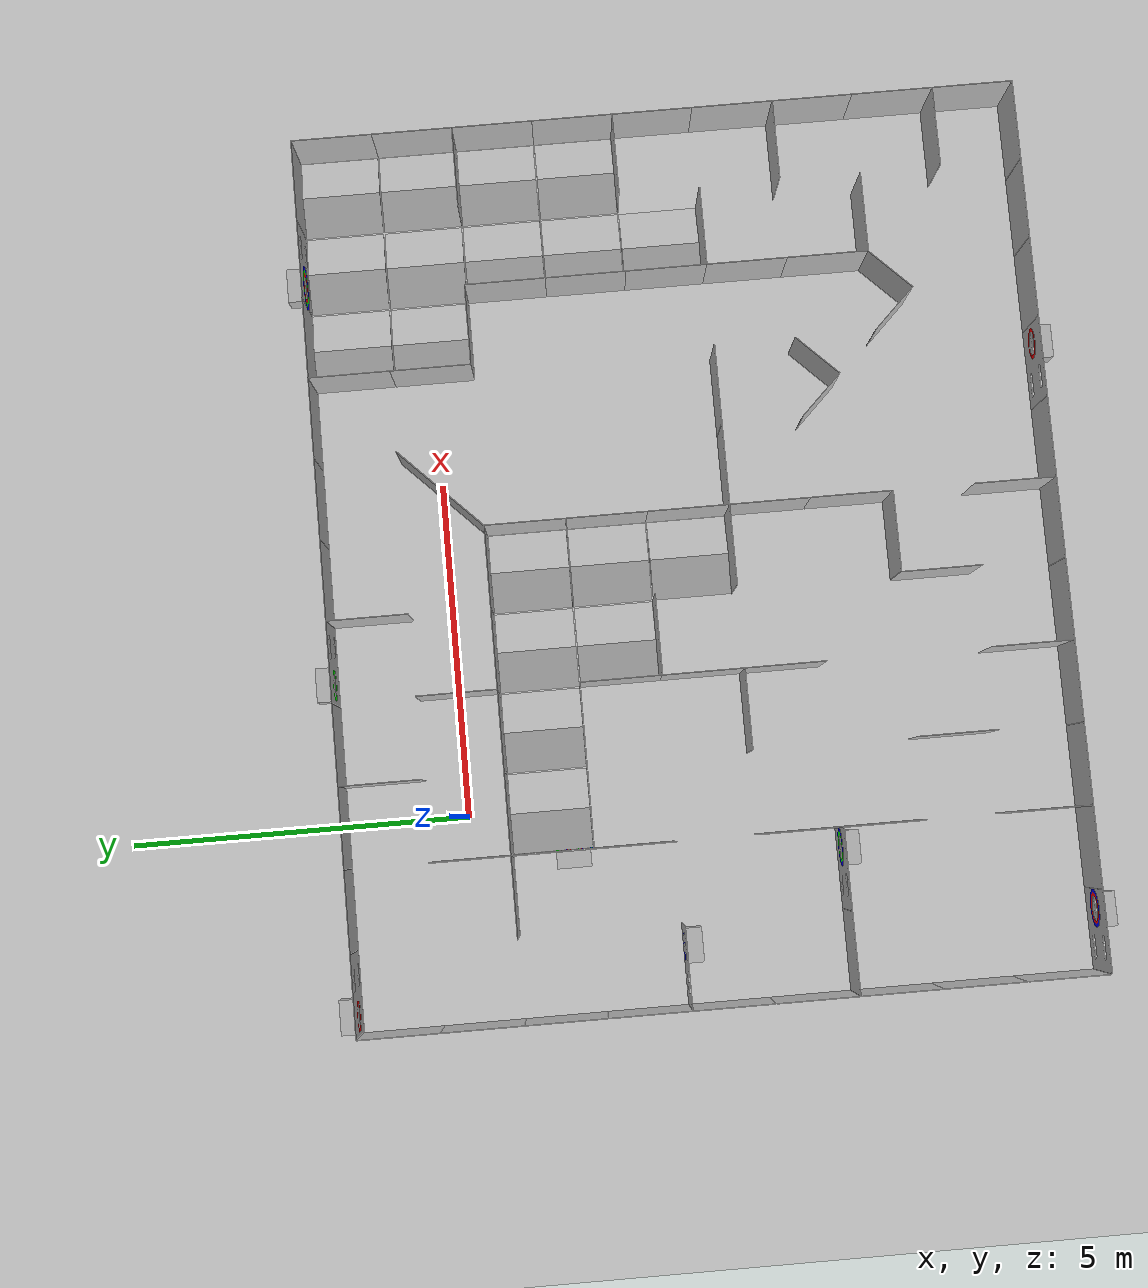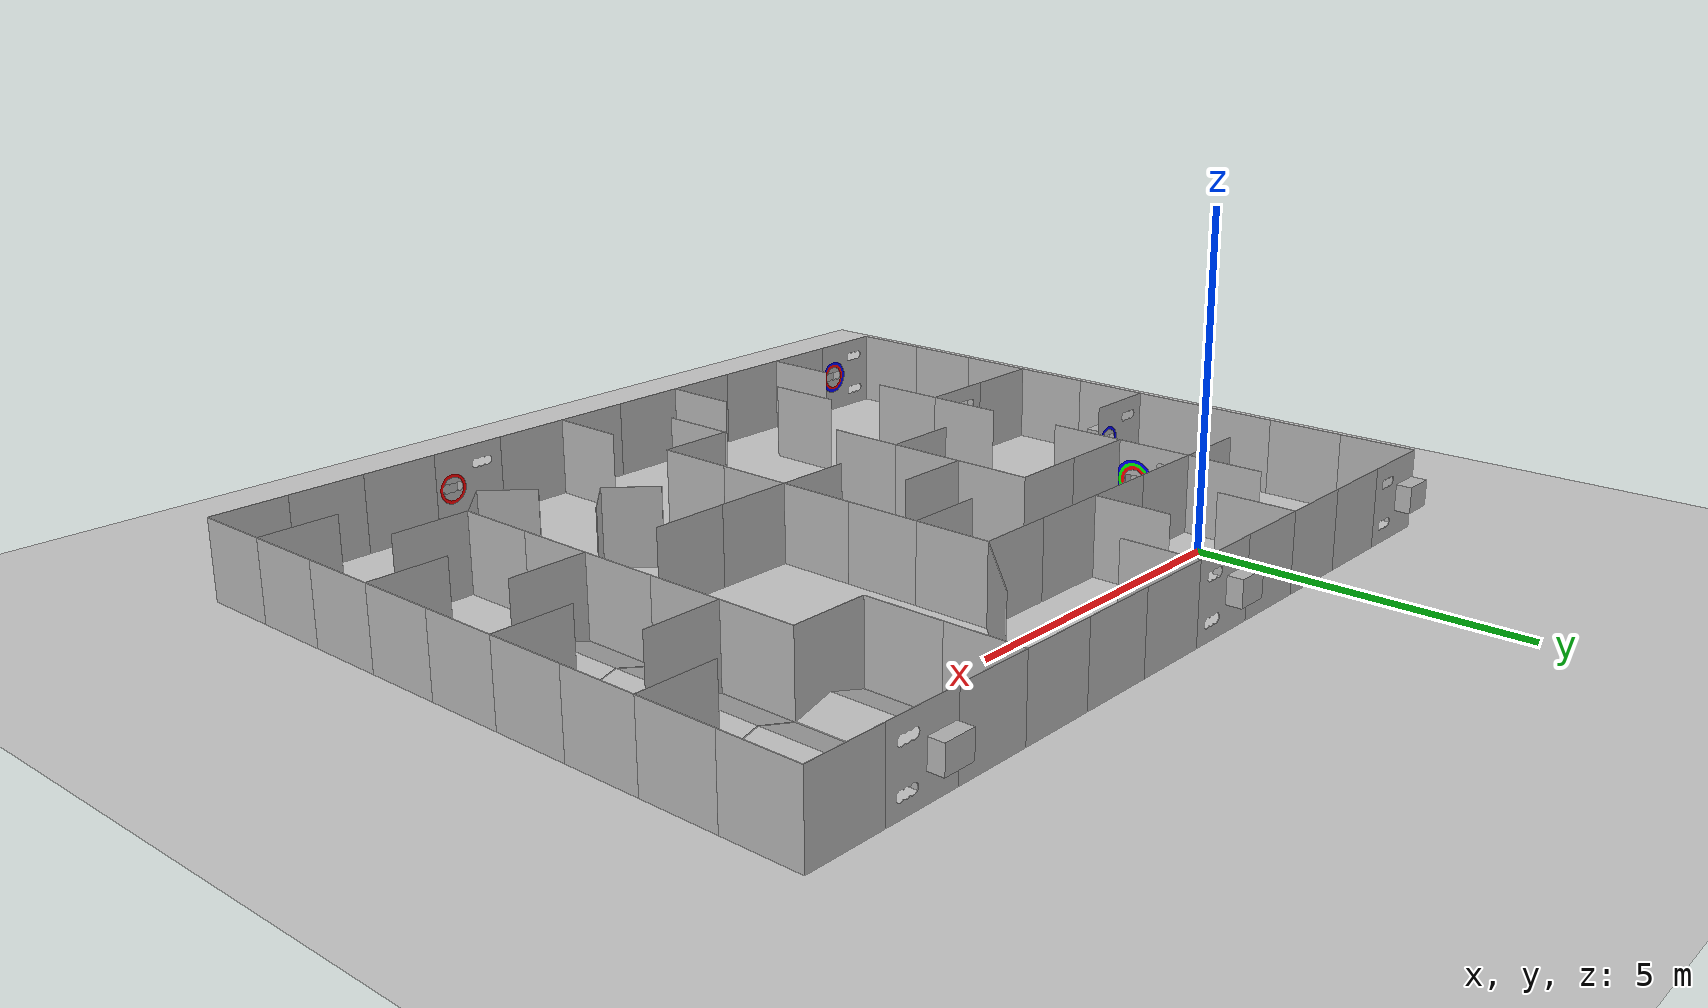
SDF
<sdf version="1.4">
 <world name="default">
  <scene><ambient>0.5 0.5 0.5 1</ambient><background>0.5 0.5 0.5 1</background><shadows>false</shadows></scene>
  <include><uri>model://sun</uri></include>
  <physics type="ode">
   <gravity>0 0 -9.81</gravity>
   <max_step_size>0.001</max_step_size>
   <real_time_factor>1</real_time_factor>
   <real_time_update_rate>1000</real_time_update_rate>
  </physics>
  <light type="directional" name="directional_light_1">
   <cast_shadows>false</cast_shadows>
   <pose>0 0 30 0.1 0.1 0</pose>
   <diffuse>.5 .5 .5 1</diffuse>
   <specular>.1 .1 .1 1</specular>
   <attenuation><range>300</range></attenuation>
   <direction>0.1 0.1 -1</direction>
  </light>
  <model name="plane_model">
   <static>true</static>
   <link name="plane_model_link">
    <collision name="plane_model_collision">
     <geometry><plane><normal>0 0 1</normal><size>100 100</size></plane></geometry>
     <surface>
      <friction>
       <ode><mu>10.0</mu><mu2>10.0</mu2><fdir1>0 0 0</fdir1><slip1>0</slip1><slip2>0</slip2></ode>
      </friction>
      <bounce><restitution_coefficient>0</restitution_coefficient><threshold>1000000.0</threshold></bounce>
      <contact>
       <ode>
        <soft_cfm>0</soft_cfm>
        <soft_erp>0.2</soft_erp>
        <kp>1e10</kp>
        <kd>1</kd>
        <max_vel>100.0</max_vel>
        <min_depth>0.0001</min_depth>
       </ode>
      </contact>
     </surface>
    </collision>
    <visual name="plane_model_visual">
     <cast_shadows>false</cast_shadows>
     <geometry><plane><normal>0 0 1</normal><size>100 100</size></plane></geometry>
     <material><script>Gazebo/Grey</script></material>
    </visual>
   </link>
  </model>
  <model name="small_wall_1">
   <static>true</static>
   <link name="small_wall_1_link">
    <pose>-3.6 1.2 0 0 0 -1.5708</pose>
    <collision name="small_wall_1_collision">
     <geometry><mesh><uri>file://robocup/walls/small_wall.dae</uri><scale>1 1 1</scale></mesh></geometry>
    </collision>
    <visual name="small_wall_1_visual">
     <cast_shadows>false</cast_shadows>
     <geometry><mesh><uri>file://robocup/walls/small_wall.dae</uri><scale>1 1 1</scale></mesh></geometry>
    </visual>
   </link>
  </model>
  <model name="small_wall_2">
   <static>true</static>
   <link name="small_wall_2_link">
    <pose>0 2.4 0 0 0 -3.14159</pose>
    <collision name="small_wall_2_collision">
     <geometry><mesh><uri>file://robocup/walls/small_wall.dae</uri><scale>1 1 1</scale></mesh></geometry>
    </collision>
    <visual name="small_wall_2_visual">
     <cast_shadows>false</cast_shadows>
     <geometry><mesh><uri>file://robocup/walls/small_wall.dae</uri><scale>1 1 1</scale></mesh></geometry>
    </visual>
   </link>
  </model>
  <model name="small_wall_3">
   <static>true</static>
   <link name="small_wall_3_link">
    <pose>1.2 2.4 0 0 0 -3.14159</pose>
    <collision name="small_wall_3_collision">
     <geometry><mesh><uri>file://robocup/walls/small_wall.dae</uri><scale>1 1 1</scale></mesh></geometry>
    </collision>
    <visual name="small_wall_3_visual">
     <cast_shadows>false</cast_shadows>
     <geometry><mesh><uri>file://robocup/walls/small_wall.dae</uri><scale>1 1 1</scale></mesh></geometry>
    </visual>
   </link>
  </model>
  <model name="small_wall_4">
   <static>true</static>
   <link name="small_wall_4_link">
    <pose>3.6 2.4 0 0 0 -3.14159</pose>
    <collision name="small_wall_4_collision">
     <geometry><mesh><uri>file://robocup/walls/small_wall.dae</uri><scale>1 1 1</scale></mesh></geometry>
    </collision>
    <visual name="small_wall_4_visual">
     <cast_shadows>false</cast_shadows>
     <geometry><mesh><uri>file://robocup/walls/small_wall.dae</uri><scale>1 1 1</scale></mesh></geometry>
    </visual>
   </link>
  </model>
  <model name="small_wall_5">
   <static>true</static>
   <link name="small_wall_5_link">
    <pose>4.8 2.4 0 0 0 -3.14159</pose>
    <collision name="small_wall_5_collision">
     <geometry><mesh><uri>file://robocup/walls/small_wall.dae</uri><scale>1 1 1</scale></mesh></geometry>
    </collision>
    <visual name="small_wall_5_visual">
     <cast_shadows>false</cast_shadows>
     <geometry><mesh><uri>file://robocup/walls/small_wall.dae</uri><scale>1 1 1</scale></mesh></geometry>
    </visual>
   </link>
  </model>
  <model name="small_wall_6">
   <static>true</static>
   <link name="small_wall_6_link">
    <pose>6 2.4 0 0 0 -3.14159</pose>
    <collision name="small_wall_6_collision">
     <geometry><mesh><uri>file://robocup/walls/small_wall.dae</uri><scale>1 1 1</scale></mesh></geometry>
    </collision>
    <visual name="small_wall_6_visual">
     <cast_shadows>false</cast_shadows>
     <geometry><mesh><uri>file://robocup/walls/small_wall.dae</uri><scale>1 1 1</scale></mesh></geometry>
    </visual>
   </link>
  </model>
  <model name="small_wall_7">
   <static>true</static>
   <link name="small_wall_7_link">
    <pose>7.2 2.4 0 0 0 -3.14159</pose>
    <collision name="small_wall_7_collision">
     <geometry><mesh><uri>file://robocup/walls/small_wall.dae</uri><scale>1 1 1</scale></mesh></geometry>
    </collision>
    <visual name="small_wall_7_visual">
     <cast_shadows>false</cast_shadows>
     <geometry><mesh><uri>file://robocup/walls/small_wall.dae</uri><scale>1 1 1</scale></mesh></geometry>
    </visual>
   </link>
  </model>
  <model name="small_wall_8">
   <static>true</static>
   <link name="small_wall_8_link">
    <pose>9.6 2.4 0 0 0 -3.14159</pose>
    <collision name="small_wall_8_collision">
     <geometry><mesh><uri>file://robocup/walls/small_wall.dae</uri><scale>1 1 1</scale></mesh></geometry>
    </collision>
    <visual name="small_wall_8_visual">
     <cast_shadows>false</cast_shadows>
     <geometry><mesh><uri>file://robocup/walls/small_wall.dae</uri><scale>1 1 1</scale></mesh></geometry>
    </visual>
   </link>
  </model>
  <model name="small_wall_9">
   <static>true</static>
   <link name="small_wall_9_link">
    <pose>10.8 1.2 0 0 0 -4.71239</pose>
    <collision name="small_wall_9_collision">
     <geometry><mesh><uri>file://robocup/walls/small_wall.dae</uri><scale>1 1 1</scale></mesh></geometry>
    </collision>
    <visual name="small_wall_9_visual">
     <cast_shadows>false</cast_shadows>
     <geometry><mesh><uri>file://robocup/walls/small_wall.dae</uri><scale>1 1 1</scale></mesh></geometry>
    </visual>
   </link>
  </model>
  <model name="small_wall_10">
   <static>true</static>
   <link name="small_wall_10_link">
    <pose>10.8 0 0 0 0 -4.71239</pose>
    <collision name="small_wall_10_collision">
     <geometry><mesh><uri>file://robocup/walls/small_wall.dae</uri><scale>1 1 1</scale></mesh></geometry>
    </collision>
    <visual name="small_wall_10_visual">
     <cast_shadows>false</cast_shadows>
     <geometry><mesh><uri>file://robocup/walls/small_wall.dae</uri><scale>1 1 1</scale></mesh></geometry>
    </visual>
   </link>
  </model>
  <model name="small_wall_11">
   <static>true</static>
   <link name="small_wall_11_link">
    <pose>10.8 -1.2 0 0 0 -4.71239</pose>
    <collision name="small_wall_11_collision">
     <geometry><mesh><uri>file://robocup/walls/small_wall.dae</uri><scale>1 1 1</scale></mesh></geometry>
    </collision>
    <visual name="small_wall_11_visual">
     <cast_shadows>false</cast_shadows>
     <geometry><mesh><uri>file://robocup/walls/small_wall.dae</uri><scale>1 1 1</scale></mesh></geometry>
    </visual>
   </link>
  </model>
  <model name="small_wall_12">
   <static>true</static>
   <link name="small_wall_12_link">
    <pose>10.8 -2.4 0 0 0 -4.71239</pose>
    <collision name="small_wall_12_collision">
     <geometry><mesh><uri>file://robocup/walls/small_wall.dae</uri><scale>1 1 1</scale></mesh></geometry>
    </collision>
    <visual name="small_wall_12_visual">
     <cast_shadows>false</cast_shadows>
     <geometry><mesh><uri>file://robocup/walls/small_wall.dae</uri><scale>1 1 1</scale></mesh></geometry>
    </visual>
   </link>
  </model>
  <model name="small_wall_13">
   <static>true</static>
   <link name="small_wall_13_link">
    <pose>-3.6 0 0 0 0 -1.5708</pose>
    <collision name="small_wall_13_collision">
     <geometry><mesh><uri>file://robocup/walls/small_wall.dae</uri><scale>1 1 1</scale></mesh></geometry>
    </collision>
    <visual name="small_wall_13_visual">
     <cast_shadows>false</cast_shadows>
     <geometry><mesh><uri>file://robocup/walls/small_wall.dae</uri><scale>1 1 1</scale></mesh></geometry>
    </visual>
   </link>
  </model>
  <model name="small_wall_14">
   <static>true</static>
   <link name="small_wall_14_link">
    <pose>-3.6 -2.4 0 0 0 -1.5708</pose>
    <collision name="small_wall_14_collision">
     <geometry><mesh><uri>file://robocup/walls/small_wall.dae</uri><scale>1 1 1</scale></mesh></geometry>
    </collision>
    <visual name="small_wall_14_visual">
     <cast_shadows>false</cast_shadows>
     <geometry><mesh><uri>file://robocup/walls/small_wall.dae</uri><scale>1 1 1</scale></mesh></geometry>
    </visual>
   </link>
  </model>
  <model name="small_wall_15">
   <static>true</static>
   <link name="small_wall_15_link">
    <pose>-3.6 -3.6 0 0 0 -1.5708</pose>
    <collision name="small_wall_15_collision">
     <geometry><mesh><uri>file://robocup/walls/small_wall.dae</uri><scale>1 1 1</scale></mesh></geometry>
    </collision>
    <visual name="small_wall_15_visual">
     <cast_shadows>false</cast_shadows>
     <geometry><mesh><uri>file://robocup/walls/small_wall.dae</uri><scale>1 1 1</scale></mesh></geometry>
    </visual>
   </link>
  </model>
  <model name="small_wall_16">
   <static>true</static>
   <link name="small_wall_16_link">
    <pose>-3.6 -4.8 0 0 0 -1.5708</pose>
    <collision name="small_wall_16_collision">
     <geometry><mesh><uri>file://robocup/walls/small_wall.dae</uri><scale>1 1 1</scale></mesh></geometry>
    </collision>
    <visual name="small_wall_16_visual">
     <cast_shadows>false</cast_shadows>
     <geometry><mesh><uri>file://robocup/walls/small_wall.dae</uri><scale>1 1 1</scale></mesh></geometry>
    </visual>
   </link>
  </model>
  <model name="small_wall_17">
   <static>true</static>
   <link name="small_wall_17_link">
    <pose>-3.6 -6 0 0 0 -1.5708</pose>
    <collision name="small_wall_17_collision">
     <geometry><mesh><uri>file://robocup/walls/small_wall.dae</uri><scale>1 1 1</scale></mesh></geometry>
    </collision>
    <visual name="small_wall_17_visual">
     <cast_shadows>false</cast_shadows>
     <geometry><mesh><uri>file://robocup/walls/small_wall.dae</uri><scale>1 1 1</scale></mesh></geometry>
    </visual>
   </link>
  </model>
  <model name="small_wall_18">
   <static>true</static>
   <link name="small_wall_18_link">
    <pose>-3.6 -7.2 0 0 0 -1.5708</pose>
    <collision name="small_wall_18_collision">
     <geometry><mesh><uri>file://robocup/walls/small_wall.dae</uri><scale>1 1 1</scale></mesh></geometry>
    </collision>
    <visual name="small_wall_18_visual">
     <cast_shadows>false</cast_shadows>
     <geometry><mesh><uri>file://robocup/walls/small_wall.dae</uri><scale>1 1 1</scale></mesh></geometry>
    </visual>
   </link>
  </model>
  <model name="small_wall_19">
   <static>true</static>
   <link name="small_wall_19_link">
    <pose>10.8 -3.6 0 0 0 -4.71239</pose>
    <collision name="small_wall_19_collision">
     <geometry><mesh><uri>file://robocup/walls/small_wall.dae</uri><scale>1 1 1</scale></mesh></geometry>
    </collision>
    <visual name="small_wall_19_visual">
     <cast_shadows>false</cast_shadows>
     <geometry><mesh><uri>file://robocup/walls/small_wall.dae</uri><scale>1 1 1</scale></mesh></geometry>
    </visual>
   </link>
  </model>
  <model name="small_wall_20">
   <static>true</static>
   <link name="small_wall_20_link">
    <pose>10.8 -4.8 0 0 0 -4.71239</pose>
    <collision name="small_wall_20_collision">
     <geometry><mesh><uri>file://robocup/walls/small_wall.dae</uri><scale>1 1 1</scale></mesh></geometry>
    </collision>
    <visual name="small_wall_20_visual">
     <cast_shadows>false</cast_shadows>
     <geometry><mesh><uri>file://robocup/walls/small_wall.dae</uri><scale>1 1 1</scale></mesh></geometry>
    </visual>
   </link>
  </model>
  <model name="small_wall_21">
   <static>true</static>
   <link name="small_wall_21_link">
    <pose>10.8 -6 0 0 0 -4.71239</pose>
    <collision name="small_wall_21_collision">
     <geometry><mesh><uri>file://robocup/walls/small_wall.dae</uri><scale>1 1 1</scale></mesh></geometry>
    </collision>
    <visual name="small_wall_21_visual">
     <cast_shadows>false</cast_shadows>
     <geometry><mesh><uri>file://robocup/walls/small_wall.dae</uri><scale>1 1 1</scale></mesh></geometry>
    </visual>
   </link>
  </model>
  <model name="small_wall_22">
   <static>true</static>
   <link name="small_wall_22_link">
    <pose>10.8 -7.2 0 0 0 -4.71239</pose>
    <collision name="small_wall_22_collision">
     <geometry><mesh><uri>file://robocup/walls/small_wall.dae</uri><scale>1 1 1</scale></mesh></geometry>
    </collision>
    <visual name="small_wall_22_visual">
     <cast_shadows>false</cast_shadows>
     <geometry><mesh><uri>file://robocup/walls/small_wall.dae</uri><scale>1 1 1</scale></mesh></geometry>
    </visual>
   </link>
  </model>
  <model name="small_wall_23">
   <static>true</static>
   <link name="small_wall_23_link">
    <pose>10.8 -8.4 0 0 0 -4.71239</pose>
    <collision name="small_wall_23_collision">
     <geometry><mesh><uri>file://robocup/walls/small_wall.dae</uri><scale>1 1 1</scale></mesh></geometry>
    </collision>
    <visual name="small_wall_23_visual">
     <cast_shadows>false</cast_shadows>
     <geometry><mesh><uri>file://robocup/walls/small_wall.dae</uri><scale>1 1 1</scale></mesh></geometry>
    </visual>
   </link>
  </model>
  <model name="small_wall_24">
   <static>true</static>
   <link name="small_wall_24_link">
    <pose>-3.6 -8.4 0 0 0 -1.5708</pose>
    <collision name="small_wall_24_collision">
     <geometry><mesh><uri>file://robocup/walls/small_wall.dae</uri><scale>1 1 1</scale></mesh></geometry>
    </collision>
    <visual name="small_wall_24_visual">
     <cast_shadows>false</cast_shadows>
     <geometry><mesh><uri>file://robocup/walls/small_wall.dae</uri><scale>1 1 1</scale></mesh></geometry>
    </visual>
   </link>
  </model>
  <model name="small_wall_25">
   <static>true</static>
   <link name="small_wall_25_link">
    <pose>-1.2 -9.6 0 0 0 0</pose>
    <collision name="small_wall_25_collision">
     <geometry><mesh><uri>file://robocup/walls/small_wall.dae</uri><scale>1 1 1</scale></mesh></geometry>
    </collision>
    <visual name="small_wall_25_visual">
     <cast_shadows>false</cast_shadows>
     <geometry><mesh><uri>file://robocup/walls/small_wall.dae</uri><scale>1 1 1</scale></mesh></geometry>
    </visual>
   </link>
  </model>
  <model name="small_wall_26">
   <static>true</static>
   <link name="small_wall_26_link">
    <pose>0 -9.6 0 0 0 0</pose>
    <collision name="small_wall_26_collision">
     <geometry><mesh><uri>file://robocup/walls/small_wall.dae</uri><scale>1 1 1</scale></mesh></geometry>
    </collision>
    <visual name="small_wall_26_visual">
     <cast_shadows>false</cast_shadows>
     <geometry><mesh><uri>file://robocup/walls/small_wall.dae</uri><scale>1 1 1</scale></mesh></geometry>
    </visual>
   </link>
  </model>
  <model name="small_wall_27">
   <static>true</static>
   <link name="small_wall_27_link">
    <pose>1.2 -9.6 0 0 0 0</pose>
    <collision name="small_wall_27_collision">
     <geometry><mesh><uri>file://robocup/walls/small_wall.dae</uri><scale>1 1 1</scale></mesh></geometry>
    </collision>
    <visual name="small_wall_27_visual">
     <cast_shadows>false</cast_shadows>
     <geometry><mesh><uri>file://robocup/walls/small_wall.dae</uri><scale>1 1 1</scale></mesh></geometry>
    </visual>
   </link>
  </model>
  <model name="small_wall_28">
   <static>true</static>
   <link name="small_wall_28_link">
    <pose>3.6 -9.6 0 0 0 0</pose>
    <collision name="small_wall_28_collision">
     <geometry><mesh><uri>file://robocup/walls/small_wall.dae</uri><scale>1 1 1</scale></mesh></geometry>
    </collision>
    <visual name="small_wall_28_visual">
     <cast_shadows>false</cast_shadows>
     <geometry><mesh><uri>file://robocup/walls/small_wall.dae</uri><scale>1 1 1</scale></mesh></geometry>
    </visual>
   </link>
  </model>
  <model name="small_wall_29">
   <static>true</static>
   <link name="small_wall_29_link">
    <pose>4.8 -9.6 0 0 0 0</pose>
    <collision name="small_wall_29_collision">
     <geometry><mesh><uri>file://robocup/walls/small_wall.dae</uri><scale>1 1 1</scale></mesh></geometry>
    </collision>
    <visual name="small_wall_29_visual">
     <cast_shadows>false</cast_shadows>
     <geometry><mesh><uri>file://robocup/walls/small_wall.dae</uri><scale>1 1 1</scale></mesh></geometry>
    </visual>
   </link>
  </model>
  <model name="small_wall_30">
   <static>true</static>
   <link name="small_wall_30_link">
    <pose>7.2 -9.6 0 0 0 0</pose>
    <collision name="small_wall_30_collision">
     <geometry><mesh><uri>file://robocup/walls/small_wall.dae</uri><scale>1 1 1</scale></mesh></geometry>
    </collision>
    <visual name="small_wall_30_visual">
     <cast_shadows>false</cast_shadows>
     <geometry><mesh><uri>file://robocup/walls/small_wall.dae</uri><scale>1 1 1</scale></mesh></geometry>
    </visual>
   </link>
  </model>
  <model name="small_wall_31">
   <static>true</static>
   <link name="small_wall_31_link">
    <pose>8.4 -9.6 0 0 0 0</pose>
    <collision name="small_wall_31_collision">
     <geometry><mesh><uri>file://robocup/walls/small_wall.dae</uri><scale>1 1 1</scale></mesh></geometry>
    </collision>
    <visual name="small_wall_31_visual">
     <cast_shadows>false</cast_shadows>
     <geometry><mesh><uri>file://robocup/walls/small_wall.dae</uri><scale>1 1 1</scale></mesh></geometry>
    </visual>
   </link>
  </model>
  <model name="small_wall_32">
   <static>true</static>
   <link name="small_wall_32_link">
    <pose>9.6 -9.6 0 0 0 0</pose>
    <collision name="small_wall_32_collision">
     <geometry><mesh><uri>file://robocup/walls/small_wall.dae</uri><scale>1 1 1</scale></mesh></geometry>
    </collision>
    <visual name="small_wall_32_visual">
     <cast_shadows>false</cast_shadows>
     <geometry><mesh><uri>file://robocup/walls/small_wall.dae</uri><scale>1 1 1</scale></mesh></geometry>
    </visual>
   </link>
  </model>
  <model name="small_wall_33">
   <static>true</static>
   <link name="small_wall_33_link">
    <pose>7.2 1.2 0 0 0 -4.71239</pose>
    <collision name="small_wall_33_collision">
     <geometry><mesh><uri>file://robocup/walls/small_wall.dae</uri><scale>1 1 1</scale></mesh></geometry>
    </collision>
    <visual name="small_wall_33_visual">
     <cast_shadows>false</cast_shadows>
     <geometry><mesh><uri>file://robocup/walls/small_wall.dae</uri><scale>1 1 1</scale></mesh></geometry>
    </visual>
   </link>
  </model>
  <model name="small_wall_34">
   <static>true</static>
   <link name="small_wall_34_link">
    <pose>7.2 0 0 0 0 -4.71239</pose>
    <collision name="small_wall_34_collision">
     <geometry><mesh><uri>file://robocup/walls/small_wall.dae</uri><scale>1 1 1</scale></mesh></geometry>
    </collision>
    <visual name="small_wall_34_visual">
     <cast_shadows>false</cast_shadows>
     <geometry><mesh><uri>file://robocup/walls/small_wall.dae</uri><scale>1 1 1</scale></mesh></geometry>
    </visual>
   </link>
  </model>
  <model name="small_wall_35">
   <static>true</static>
   <link name="small_wall_35_link">
    <pose>7.2 0 0 0 0 -3.14159</pose>
    <collision name="small_wall_35_collision">
     <geometry><mesh><uri>file://robocup/walls/small_wall.dae</uri><scale>1 1 1</scale></mesh></geometry>
    </collision>
    <visual name="small_wall_35_visual">
     <cast_shadows>false</cast_shadows>
     <geometry><mesh><uri>file://robocup/walls/small_wall.dae</uri><scale>1 1 1</scale></mesh></geometry>
    </visual>
   </link>
  </model>
  <model name="small_wall_36">
   <static>true</static>
   <link name="small_wall_36_link">
    <pose>7.2 -1.2 0 0 0 -1.5708</pose>
    <collision name="small_wall_36_collision">
     <geometry><mesh><uri>file://robocup/walls/small_wall.dae</uri><scale>1 1 1</scale></mesh></geometry>
    </collision>
    <visual name="small_wall_36_visual">
     <cast_shadows>false</cast_shadows>
     <geometry><mesh><uri>file://robocup/walls/small_wall.dae</uri><scale>1 1 1</scale></mesh></geometry>
    </visual>
   </link>
  </model>
  <model name="small_wall_37">
   <static>true</static>
   <link name="small_wall_37_link">
    <pose>8.4 -2.4 0 0 0 -4.71239</pose>
    <collision name="small_wall_37_collision">
     <geometry><mesh><uri>file://robocup/walls/small_wall.dae</uri><scale>1 1 1</scale></mesh></geometry>
    </collision>
    <visual name="small_wall_37_visual">
     <cast_shadows>false</cast_shadows>
     <geometry><mesh><uri>file://robocup/walls/small_wall.dae</uri><scale>1 1 1</scale></mesh></geometry>
    </visual>
   </link>
  </model>
  <model name="small_wall_38">
   <static>true</static>
   <link name="small_wall_38_link">
    <pose>7.2 -3.6 0 0 0 -1.5708</pose>
    <collision name="small_wall_38_collision">
     <geometry><mesh><uri>file://robocup/walls/small_wall.dae</uri><scale>1 1 1</scale></mesh></geometry>
    </collision>
    <visual name="small_wall_38_visual">
     <cast_shadows>false</cast_shadows>
     <geometry><mesh><uri>file://robocup/walls/small_wall.dae</uri><scale>1 1 1</scale></mesh></geometry>
    </visual>
   </link>
  </model>
  <model name="small_wall_39">
   <static>true</static>
   <link name="small_wall_39_link">
    <pose>8.4 -4.8 0 0 0 -4.71239</pose>
    <collision name="small_wall_39_collision">
     <geometry><mesh><uri>file://robocup/walls/small_wall.dae</uri><scale>1 1 1</scale></mesh></geometry>
    </collision>
    <visual name="small_wall_39_visual">
     <cast_shadows>false</cast_shadows>
     <geometry><mesh><uri>file://robocup/walls/small_wall.dae</uri><scale>1 1 1</scale></mesh></geometry>
    </visual>
   </link>
  </model>
  <model name="small_wall_40">
   <static>true</static>
   <link name="small_wall_40_link">
    <pose>7.2 -6 0 0 0 -1.5708</pose>
    <collision name="small_wall_40_collision">
     <geometry><mesh><uri>file://robocup/walls/small_wall.dae</uri><scale>1 1 1</scale></mesh></geometry>
    </collision>
    <visual name="small_wall_40_visual">
     <cast_shadows>false</cast_shadows>
     <geometry><mesh><uri>file://robocup/walls/small_wall.dae</uri><scale>1 1 1</scale></mesh></geometry>
    </visual>
   </link>
  </model>
  <model name="small_wall_41">
   <static>true</static>
   <link name="small_wall_41_link">
    <pose>1.2 -2.4 0 0 0 0</pose>
    <collision name="small_wall_41_collision">
     <geometry><mesh><uri>file://robocup/walls/small_wall.dae</uri><scale>1 1 1</scale></mesh></geometry>
    </collision>
    <visual name="small_wall_41_visual">
     <cast_shadows>false</cast_shadows>
     <geometry><mesh><uri>file://robocup/walls/small_wall.dae</uri><scale>1 1 1</scale></mesh></geometry>
    </visual>
   </link>
  </model>
  <model name="small_wall_42">
   <static>true</static>
   <link name="small_wall_42_link">
    <pose>0 -1.2 0 0 0 -3.14159</pose>
    <collision name="small_wall_42_collision">
     <geometry><mesh><uri>file://robocup/walls/small_wall.dae</uri><scale>1 1 1</scale></mesh></geometry>
    </collision>
    <visual name="small_wall_42_visual">
     <cast_shadows>false</cast_shadows>
     <geometry><mesh><uri>file://robocup/walls/small_wall.dae</uri><scale>1 1 1</scale></mesh></geometry>
    </visual>
   </link>
  </model>
  <model name="small_wall_43">
   <static>true</static>
   <link name="small_wall_43_link">
    <pose>0 -1.2 0 0 0 0</pose>
    <collision name="small_wall_43_collision">
     <geometry><mesh><uri>file://robocup/walls/small_wall.dae</uri><scale>1 1 1</scale></mesh></geometry>
    </collision>
    <visual name="small_wall_43_visual">
     <cast_shadows>false</cast_shadows>
     <geometry><mesh><uri>file://robocup/walls/small_wall.dae</uri><scale>1 1 1</scale></mesh></geometry>
    </visual>
   </link>
  </model>
  <model name="small_wall_44">
   <static>true</static>
   <link name="small_wall_44_link">
    <pose>1.2 -1.2 0 0 0 0</pose>
    <collision name="small_wall_44_collision">
     <geometry><mesh><uri>file://robocup/walls/small_wall.dae</uri><scale>1 1 1</scale></mesh></geometry>
    </collision>
    <visual name="small_wall_44_visual">
     <cast_shadows>false</cast_shadows>
     <geometry><mesh><uri>file://robocup/walls/small_wall.dae</uri><scale>1 1 1</scale></mesh></geometry>
    </visual>
   </link>
  </model>
  <model name="small_wall_45">
   <static>true</static>
   <link name="small_wall_45_link">
    <pose>2.4 0 0 0 0 -3.14159</pose>
    <collision name="small_wall_45_collision">
     <geometry><mesh><uri>file://robocup/walls/small_wall.dae</uri><scale>1 1 1</scale></mesh></geometry>
    </collision>
    <visual name="small_wall_45_visual">
     <cast_shadows>false</cast_shadows>
     <geometry><mesh><uri>file://robocup/walls/small_wall.dae</uri><scale>1 1 1</scale></mesh></geometry>
    </visual>
   </link>
  </model>
  <model name="small_wall_46">
   <static>true</static>
   <link name="small_wall_46_link">
    <pose>3.6 -1.2 0 0 0 0</pose>
    <collision name="small_wall_46_collision">
     <geometry><mesh><uri>file://robocup/walls/small_wall.dae</uri><scale>1 1 1</scale></mesh></geometry>
    </collision>
    <visual name="small_wall_46_visual">
     <cast_shadows>false</cast_shadows>
     <geometry><mesh><uri>file://robocup/walls/small_wall.dae</uri><scale>1 1 1</scale></mesh></geometry>
    </visual>
   </link>
  </model>
  <model name="small_wall_47">
   <static>true</static>
   <link name="small_wall_47_link">
    <pose>1.2 -2.4 0 0 0 -1.5708</pose>
    <collision name="small_wall_47_collision">
     <geometry><mesh><uri>file://robocup/walls/small_wall.dae</uri><scale>1 1 1</scale></mesh></geometry>
    </collision>
    <visual name="small_wall_47_visual">
     <cast_shadows>false</cast_shadows>
     <geometry><mesh><uri>file://robocup/walls/small_wall.dae</uri><scale>1 1 1</scale></mesh></geometry>
    </visual>
   </link>
  </model>
  <model name="small_wall_48">
   <static>true</static>
   <link name="small_wall_48_link">
    <pose>1.2 -3.6 0 0 0 -1.5708</pose>
    <collision name="small_wall_48_collision">
     <geometry><mesh><uri>file://robocup/walls/small_wall.dae</uri><scale>1 1 1</scale></mesh></geometry>
    </collision>
    <visual name="small_wall_48_visual">
     <cast_shadows>false</cast_shadows>
     <geometry><mesh><uri>file://robocup/walls/small_wall.dae</uri><scale>1 1 1</scale></mesh></geometry>
    </visual>
   </link>
  </model>
  <model name="small_wall_49">
   <static>true</static>
   <link name="small_wall_49_link">
    <pose>3.6 -2.4 0 0 0 -1.5708</pose>
    <collision name="small_wall_49_collision">
     <geometry><mesh><uri>file://robocup/walls/small_wall.dae</uri><scale>1 1 1</scale></mesh></geometry>
    </collision>
    <visual name="small_wall_49_visual">
     <cast_shadows>false</cast_shadows>
     <geometry><mesh><uri>file://robocup/walls/small_wall.dae</uri><scale>1 1 1</scale></mesh></geometry>
    </visual>
   </link>
  </model>
  <model name="small_wall_50">
   <static>true</static>
   <link name="small_wall_50_link">
    <pose>3.6 -3.6 0 0 0 -1.5708</pose>
    <collision name="small_wall_50_collision">
     <geometry><mesh><uri>file://robocup/walls/small_wall.dae</uri><scale>1 1 1</scale></mesh></geometry>
    </collision>
    <visual name="small_wall_50_visual">
     <cast_shadows>false</cast_shadows>
     <geometry><mesh><uri>file://robocup/walls/small_wall.dae</uri><scale>1 1 1</scale></mesh></geometry>
    </visual>
   </link>
  </model>
  <model name="small_wall_51">
   <static>true</static>
   <link name="small_wall_51_link">
    <pose>4.8 -4.8 0 0 0 0</pose>
    <collision name="small_wall_51_collision">
     <geometry><mesh><uri>file://robocup/walls/small_wall.dae</uri><scale>1 1 1</scale></mesh></geometry>
    </collision>
    <visual name="small_wall_51_visual">
     <cast_shadows>false</cast_shadows>
     <geometry><mesh><uri>file://robocup/walls/small_wall.dae</uri><scale>1 1 1</scale></mesh></geometry>
    </visual>
   </link>
  </model>
  <model name="small_wall_52">
   <static>true</static>
   <link name="small_wall_52_link">
    <pose>3.6 -4.8 0 0 0 -1.5708</pose>
    <collision name="small_wall_52_collision">
     <geometry><mesh><uri>file://robocup/walls/small_wall.dae</uri><scale>1 1 1</scale></mesh></geometry>
    </collision>
    <visual name="small_wall_52_visual">
     <cast_shadows>false</cast_shadows>
     <geometry><mesh><uri>file://robocup/walls/small_wall.dae</uri><scale>1 1 1</scale></mesh></geometry>
    </visual>
   </link>
  </model>
  <model name="small_wall_53">
   <static>true</static>
   <link name="small_wall_53_link">
    <pose>2.4 -4.8 0 0 0 -4.71239</pose>
    <collision name="small_wall_53_collision">
     <geometry><mesh><uri>file://robocup/walls/small_wall.dae</uri><scale>1 1 1</scale></mesh></geometry>
    </collision>
    <visual name="small_wall_53_visual">
     <cast_shadows>false</cast_shadows>
     <geometry><mesh><uri>file://robocup/walls/small_wall.dae</uri><scale>1 1 1</scale></mesh></geometry>
    </visual>
   </link>
  </model>
  <model name="small_wall_54">
   <static>true</static>
   <link name="small_wall_54_link">
    <pose>-2.4 -6 0 0 0 0</pose>
    <collision name="small_wall_54_collision">
     <geometry><mesh><uri>file://robocup/walls/small_wall.dae</uri><scale>1 1 1</scale></mesh></geometry>
    </collision>
    <visual name="small_wall_54_visual">
     <cast_shadows>false</cast_shadows>
     <geometry><mesh><uri>file://robocup/walls/small_wall.dae</uri><scale>1 1 1</scale></mesh></geometry>
    </visual>
   </link>
  </model>
  <model name="small_wall_55">
   <static>true</static>
   <link name="small_wall_55_link">
    <pose>-1.2 -6 0 0 0 -1.5708</pose>
    <collision name="small_wall_55_collision">
     <geometry><mesh><uri>file://robocup/walls/small_wall.dae</uri><scale>1 1 1</scale></mesh></geometry>
    </collision>
    <visual name="small_wall_55_visual">
     <cast_shadows>false</cast_shadows>
     <geometry><mesh><uri>file://robocup/walls/small_wall.dae</uri><scale>1 1 1</scale></mesh></geometry>
    </visual>
   </link>
  </model>
  <model name="small_wall_56">
   <static>true</static>
   <link name="small_wall_56_link">
    <pose>4.8 -6 0 0 0 -4.71239</pose>
    <collision name="small_wall_56_collision">
     <geometry><mesh><uri>file://robocup/walls/small_wall.dae</uri><scale>1 1 1</scale></mesh></geometry>
    </collision>
    <visual name="small_wall_56_visual">
     <cast_shadows>false</cast_shadows>
     <geometry><mesh><uri>file://robocup/walls/small_wall.dae</uri><scale>1 1 1</scale></mesh></geometry>
    </visual>
   </link>
  </model>
  <model name="small_wall_57">
   <static>true</static>
   <link name="small_wall_57_link">
    <pose>3.6 -6 0 0 0 -3.14159</pose>
    <collision name="small_wall_57_collision">
     <geometry><mesh><uri>file://robocup/walls/small_wall.dae</uri><scale>1 1 1</scale></mesh></geometry>
    </collision>
    <visual name="small_wall_57_visual">
     <cast_shadows>false</cast_shadows>
     <geometry><mesh><uri>file://robocup/walls/small_wall.dae</uri><scale>1 1 1</scale></mesh></geometry>
    </visual>
   </link>
  </model>
  <model name="half_ramp_1">
   <static>true</static>
   <link name="half_ramp_1_link">
    <pose>9.6 -1.2 0 0 0 -1.5708</pose>
    <collision name="half_ramp_1_collision">
     <geometry><mesh><uri>file://robocup/ramps/half_ramp.dae</uri><scale>1 1 1</scale></mesh></geometry>
    </collision>
    <visual name="half_ramp_1_visual">
     <cast_shadows>false</cast_shadows>
     <geometry><mesh><uri>file://robocup/ramps/half_ramp.dae</uri><scale>1 1 1</scale></mesh></geometry>
    </visual>
   </link>
  </model>
  <model name="half_ramp_2">
   <static>true</static>
   <link name="half_ramp_2_link">
    <pose>8.4 -1.2 0 0 0 -1.5708</pose>
    <collision name="half_ramp_2_collision">
     <geometry><mesh><uri>file://robocup/ramps/half_ramp.dae</uri><scale>1 1 1</scale></mesh></geometry>
    </collision>
    <visual name="half_ramp_2_visual">
     <cast_shadows>false</cast_shadows>
     <geometry><mesh><uri>file://robocup/ramps/half_ramp.dae</uri><scale>1 1 1</scale></mesh></geometry>
    </visual>
   </link>
  </model>
  <model name="half_ramp_3">
   <static>true</static>
   <link name="half_ramp_3_link">
    <pose>8.4 -1.2 0 0 0 -4.71239</pose>
    <collision name="half_ramp_3_collision">
     <geometry><mesh><uri>file://robocup/ramps/half_ramp.dae</uri><scale>1 1 1</scale></mesh></geometry>
    </collision>
    <visual name="half_ramp_3_visual">
     <cast_shadows>false</cast_shadows>
     <geometry><mesh><uri>file://robocup/ramps/half_ramp.dae</uri><scale>1 1 1</scale></mesh></geometry>
    </visual>
   </link>
  </model>
  <model name="half_ramp_4">
   <static>true</static>
   <link name="half_ramp_4_link">
    <pose>9.6 -1.2 0 0 0 -4.71239</pose>
    <collision name="half_ramp_4_collision">
     <geometry><mesh><uri>file://robocup/ramps/half_ramp.dae</uri><scale>1 1 1</scale></mesh></geometry>
    </collision>
    <visual name="half_ramp_4_visual">
     <cast_shadows>false</cast_shadows>
     <geometry><mesh><uri>file://robocup/ramps/half_ramp.dae</uri><scale>1 1 1</scale></mesh></geometry>
    </visual>
   </link>
  </model>
  <model name="half_ramp_5">
   <static>true</static>
   <link name="half_ramp_5_link">
    <pose>8.4 0 0 0 0 -1.5708</pose>
    <collision name="half_ramp_5_collision">
     <geometry><mesh><uri>file://robocup/ramps/half_ramp.dae</uri><scale>1 1 1</scale></mesh></geometry>
    </collision>
    <visual name="half_ramp_5_visual">
     <cast_shadows>false</cast_shadows>
     <geometry><mesh><uri>file://robocup/ramps/half_ramp.dae</uri><scale>1 1 1</scale></mesh></geometry>
    </visual>
   </link>
  </model>
  <model name="half_ramp_6">
   <static>true</static>
   <link name="half_ramp_6_link">
    <pose>8.4 0 0 0 0 -4.71239</pose>
    <collision name="half_ramp_6_collision">
     <geometry><mesh><uri>file://robocup/ramps/half_ramp.dae</uri><scale>1 1 1</scale></mesh></geometry>
    </collision>
    <visual name="half_ramp_6_visual">
     <cast_shadows>false</cast_shadows>
     <geometry><mesh><uri>file://robocup/ramps/half_ramp.dae</uri><scale>1 1 1</scale></mesh></geometry>
    </visual>
   </link>
  </model>
  <model name="half_ramp_7">
   <static>true</static>
   <link name="half_ramp_7_link">
    <pose>9.6 0 0 0 0 -1.5708</pose>
    <collision name="half_ramp_7_collision">
     <geometry><mesh><uri>file://robocup/ramps/half_ramp.dae</uri><scale>1 1 1</scale></mesh></geometry>
    </collision>
    <visual name="half_ramp_7_visual">
     <cast_shadows>false</cast_shadows>
     <geometry><mesh><uri>file://robocup/ramps/half_ramp.dae</uri><scale>1 1 1</scale></mesh></geometry>
    </visual>
   </link>
  </model>
  <model name="half_ramp_8">
   <static>true</static>
   <link name="half_ramp_8_link">
    <pose>9.6 0 0 0 0 -4.71239</pose>
    <collision name="half_ramp_8_collision">
     <geometry><mesh><uri>file://robocup/ramps/half_ramp.dae</uri><scale>1 1 1</scale></mesh></geometry>
    </collision>
    <visual name="half_ramp_8_visual">
     <cast_shadows>false</cast_shadows>
     <geometry><mesh><uri>file://robocup/ramps/half_ramp.dae</uri><scale>1 1 1</scale></mesh></geometry>
    </visual>
   </link>
  </model>
  <model name="half_ramp_9">
   <static>true</static>
   <link name="half_ramp_9_link">
    <pose>8.4 -2.4 0 0 0 -1.5708</pose>
    <collision name="half_ramp_9_collision">
     <geometry><mesh><uri>file://robocup/ramps/half_ramp.dae</uri><scale>1 1 1</scale></mesh></geometry>
    </collision>
    <visual name="half_ramp_9_visual">
     <cast_shadows>false</cast_shadows>
     <geometry><mesh><uri>file://robocup/ramps/half_ramp.dae</uri><scale>1 1 1</scale></mesh></geometry>
    </visual>
   </link>
  </model>
  <model name="half_ramp_10">
   <static>true</static>
   <link name="half_ramp_10_link">
    <pose>8.4 -3.6 0 0 0 -4.71239</pose>
    <collision name="half_ramp_10_collision">
     <geometry><mesh><uri>file://robocup/ramps/half_ramp.dae</uri><scale>1 1 1</scale></mesh></geometry>
    </collision>
    <visual name="half_ramp_10_visual">
     <cast_shadows>false</cast_shadows>
     <geometry><mesh><uri>file://robocup/ramps/half_ramp.dae</uri><scale>1 1 1</scale></mesh></geometry>
    </visual>
   </link>
  </model>
  <model name="half_ramp_11">
   <static>true</static>
   <link name="half_ramp_11_link">
    <pose>9.6 -2.4 0 0 0 -1.5708</pose>
    <collision name="half_ramp_11_collision">
     <geometry><mesh><uri>file://robocup/ramps/half_ramp.dae</uri><scale>1 1 1</scale></mesh></geometry>
    </collision>
    <visual name="half_ramp_11_visual">
     <cast_shadows>false</cast_shadows>
     <geometry><mesh><uri>file://robocup/ramps/half_ramp.dae</uri><scale>1 1 1</scale></mesh></geometry>
    </visual>
   </link>
  </model>
  <model name="half_ramp_12">
   <static>true</static>
   <link name="half_ramp_12_link">
    <pose>9.6 -2.4 0 0 0 -4.71239</pose>
    <collision name="half_ramp_12_collision">
     <geometry><mesh><uri>file://robocup/ramps/half_ramp.dae</uri><scale>1 1 1</scale></mesh></geometry>
    </collision>
    <visual name="half_ramp_12_visual">
     <cast_shadows>false</cast_shadows>
     <geometry><mesh><uri>file://robocup/ramps/half_ramp.dae</uri><scale>1 1 1</scale></mesh></geometry>
    </visual>
   </link>
  </model>
  <model name="half_ramp_13">
   <static>true</static>
   <link name="half_ramp_13_link">
    <pose>8.4 -2.4 0 0 0 -4.71239</pose>
    <collision name="half_ramp_13_collision">
     <geometry><mesh><uri>file://robocup/ramps/half_ramp.dae</uri><scale>1 1 1</scale></mesh></geometry>
    </collision>
    <visual name="half_ramp_13_visual">
     <cast_shadows>false</cast_shadows>
     <geometry><mesh><uri>file://robocup/ramps/half_ramp.dae</uri><scale>1 1 1</scale></mesh></geometry>
    </visual>
   </link>
  </model>
  <model name="small_wall_58">
   <static>true</static>
   <link name="small_wall_58_link">
    <pose>9.6 -3.6 0 0 0 0</pose>
    <collision name="small_wall_58_collision">
     <geometry><mesh><uri>file://robocup/walls/small_wall.dae</uri><scale>1 1 1</scale></mesh></geometry>
    </collision>
    <visual name="small_wall_58_visual">
     <cast_shadows>false</cast_shadows>
     <geometry><mesh><uri>file://robocup/walls/small_wall.dae</uri><scale>1 1 1</scale></mesh></geometry>
    </visual>
   </link>
  </model>
  <model name="small_wall_59">
   <static>true</static>
   <link name="small_wall_59_link">
    <pose>8.4 -1.2 0 0 0 -3.14159</pose>
    <collision name="small_wall_59_collision">
     <geometry><mesh><uri>file://robocup/walls/small_wall.dae</uri><scale>1 1 1</scale></mesh></geometry>
    </collision>
    <visual name="small_wall_59_visual">
     <cast_shadows>false</cast_shadows>
     <geometry><mesh><uri>file://robocup/walls/small_wall.dae</uri><scale>1 1 1</scale></mesh></geometry>
    </visual>
   </link>
  </model>
  <model name="small_wall_60">
   <static>true</static>
   <link name="small_wall_60_link">
    <pose>9.6 -1.2 0 0 0 0</pose>
    <collision name="small_wall_60_collision">
     <geometry><mesh><uri>file://robocup/walls/small_wall.dae</uri><scale>1 1 1</scale></mesh></geometry>
    </collision>
    <visual name="small_wall_60_visual">
     <cast_shadows>false</cast_shadows>
     <geometry><mesh><uri>file://robocup/walls/small_wall.dae</uri><scale>1 1 1</scale></mesh></geometry>
    </visual>
   </link>
  </model>
  <model name="half_ramp_14">
   <static>true</static>
   <link name="half_ramp_14_link">
    <pose>8.4 -3.6 0 0 0 -1.5708</pose>
    <collision name="half_ramp_14_collision">
     <geometry><mesh><uri>file://robocup/ramps/half_ramp.dae</uri><scale>1 1 1</scale></mesh></geometry>
    </collision>
    <visual name="half_ramp_14_visual">
     <cast_shadows>false</cast_shadows>
     <geometry><mesh><uri>file://robocup/ramps/half_ramp.dae</uri><scale>1 1 1</scale></mesh></geometry>
    </visual>
   </link>
  </model>
  <model name="small_wall_61">
   <static>true</static>
   <link name="small_wall_61_link">
    <pose>8.4 -4.8 0 0 0 0</pose>
    <collision name="small_wall_61_collision">
     <geometry><mesh><uri>file://robocup/walls/small_wall.dae</uri><scale>1 1 1</scale></mesh></geometry>
    </collision>
    <visual name="small_wall_61_visual">
     <cast_shadows>false</cast_shadows>
     <geometry><mesh><uri>file://robocup/walls/small_wall.dae</uri><scale>1 1 1</scale></mesh></geometry>
    </visual>
   </link>
  </model>
  <model name="small_wall_62">
   <static>true</static>
   <link name="small_wall_62_link">
    <pose>9.6 -4.8 0 0 0 -3.14159</pose>
    <collision name="small_wall_62_collision">
     <geometry><mesh><uri>file://robocup/walls/small_wall.dae</uri><scale>1 1 1</scale></mesh></geometry>
    </collision>
    <visual name="small_wall_62_visual">
     <cast_shadows>false</cast_shadows>
     <geometry><mesh><uri>file://robocup/walls/small_wall.dae</uri><scale>1 1 1</scale></mesh></geometry>
    </visual>
   </link>
  </model>
  <model name="small_wall_63">
   <static>true</static>
   <link name="small_wall_63_link">
    <pose>9.6 -8.4 0 0 0 0</pose>
    <collision name="small_wall_63_collision">
     <geometry><mesh><uri>file://robocup/walls/small_wall.dae</uri><scale>1 1 1</scale></mesh></geometry>
    </collision>
    <visual name="small_wall_63_visual">
     <cast_shadows>false</cast_shadows>
     <geometry><mesh><uri>file://robocup/walls/small_wall.dae</uri><scale>1 1 1</scale></mesh></geometry>
    </visual>
   </link>
  </model>
  <model name="small_wall_triple_holes_1">
   <static>true</static>
   <link name="small_wall_triple_holes_1_link">
    <pose>-2.4 -3.6 0 0 0 0</pose>
    <collision name="small_wall_triple_holes_1_collision">
     <geometry>
      <mesh><uri>file://robocup/walls/small_wall_triple_holes.dae</uri><scale>1 1 1</scale></mesh>
     </geometry>
    </collision>
    <visual name="small_wall_triple_holes_1_visual">
     <cast_shadows>false</cast_shadows>
     <geometry>
      <mesh><uri>file://robocup/walls/small_wall_triple_holes.dae</uri><scale>1 1 1</scale></mesh>
     </geometry>
    </visual>
   </link>
  </model>
  <model name="wall_diag_120_1">
   <static>true</static>
   <link name="wall_diag_120_1_link">
    <pose>4.8 0 0 0 0 0</pose>
    <collision name="wall_diag_120_1_collision">
     <geometry><mesh><uri>file://robocup/walls/wall_diag_120.dae</uri><scale>1 1 1</scale></mesh></geometry>
    </collision>
    <visual name="wall_diag_120_1_visual">
     <cast_shadows>false</cast_shadows>
     <geometry><mesh><uri>file://robocup/walls/wall_diag_120.dae</uri><scale>1 1 1</scale></mesh></geometry>
    </visual>
   </link>
  </model>
  <model name="corner_diag_120_1">
   <static>true</static>
   <link name="corner_diag_120_1_link">
    <pose>6 -6 0 0 0 0</pose>
    <collision name="corner_diag_120_1_collision">
     <geometry><mesh><uri>file://robocup/walls/corner_diag_120.dae</uri><scale>1 1 1</scale></mesh></geometry>
    </collision>
    <visual name="corner_diag_120_1_visual">
     <cast_shadows>false</cast_shadows>
     <geometry><mesh><uri>file://robocup/walls/corner_diag_120.dae</uri><scale>1 1 1</scale></mesh></geometry>
    </visual>
   </link>
  </model>
  <model name="corner_diag_120_2">
   <static>true</static>
   <link name="corner_diag_120_2_link">
    <pose>7.2 -7.2 0 0 0 0</pose>
    <collision name="corner_diag_120_2_collision">
     <geometry><mesh><uri>file://robocup/walls/corner_diag_120.dae</uri><scale>1 1 1</scale></mesh></geometry>
    </collision>
    <visual name="corner_diag_120_2_visual">
     <cast_shadows>false</cast_shadows>
     <geometry><mesh><uri>file://robocup/walls/corner_diag_120.dae</uri><scale>1 1 1</scale></mesh></geometry>
    </visual>
   </link>
  </model>
  <model name="small_wall_triple_holes_2">
   <static>true</static>
   <link name="small_wall_triple_holes_2_link">
    <pose>-2.4 2.4 0 0 0 -3.14159</pose>
    <collision name="small_wall_triple_holes_2_collision">
     <geometry>
      <mesh><uri>file://robocup/walls/small_wall_triple_holes.dae</uri><scale>1 1 1</scale></mesh>
     </geometry>
    </collision>
    <visual name="small_wall_triple_holes_2_visual">
     <cast_shadows>false</cast_shadows>
     <geometry>
      <mesh><uri>file://robocup/walls/small_wall_triple_holes.dae</uri><scale>1 1 1</scale></mesh>
     </geometry>
    </visual>
   </link>
  </model>
  <model name="small_wall_triple_holes_3">
   <static>true</static>
   <link name="small_wall_triple_holes_3_link">
    <pose>8.4 2.4 0 0 0 -3.14159</pose>
    <collision name="small_wall_triple_holes_3_collision">
     <geometry>
      <mesh><uri>file://robocup/walls/small_wall_triple_holes.dae</uri><scale>1 1 1</scale></mesh>
     </geometry>
    </collision>
    <visual name="small_wall_triple_holes_3_visual">
     <cast_shadows>false</cast_shadows>
     <geometry>
      <mesh><uri>file://robocup/walls/small_wall_triple_holes.dae</uri><scale>1 1 1</scale></mesh>
     </geometry>
    </visual>
   </link>
  </model>
  <model name="half_ramp_15">
   <static>true</static>
   <link name="half_ramp_15_link">
    <pose>9.6 1.2 0 0 0 -4.71239</pose>
    <collision name="half_ramp_15_collision">
     <geometry><mesh><uri>file://robocup/ramps/half_ramp.dae</uri><scale>1 1 1</scale></mesh></geometry>
    </collision>
    <visual name="half_ramp_15_visual">
     <cast_shadows>false</cast_shadows>
     <geometry><mesh><uri>file://robocup/ramps/half_ramp.dae</uri><scale>1 1 1</scale></mesh></geometry>
    </visual>
   </link>
  </model>
  <model name="half_ramp_16">
   <static>true</static>
   <link name="half_ramp_16_link">
    <pose>9.6 1.2 0 0 0 -1.5708</pose>
    <collision name="half_ramp_16_collision">
     <geometry><mesh><uri>file://robocup/ramps/half_ramp.dae</uri><scale>1 1 1</scale></mesh></geometry>
    </collision>
    <visual name="half_ramp_16_visual">
     <cast_shadows>false</cast_shadows>
     <geometry><mesh><uri>file://robocup/ramps/half_ramp.dae</uri><scale>1 1 1</scale></mesh></geometry>
    </visual>
   </link>
  </model>
  <model name="half_ramp_17">
   <static>true</static>
   <link name="half_ramp_17_link">
    <pose>7.2 1.2 0 0 0 -1.5708</pose>
    <collision name="half_ramp_17_collision">
     <geometry><mesh><uri>file://robocup/ramps/half_ramp.dae</uri><scale>1 1 1</scale></mesh></geometry>
    </collision>
    <visual name="half_ramp_17_visual">
     <cast_shadows>false</cast_shadows>
     <geometry><mesh><uri>file://robocup/ramps/half_ramp.dae</uri><scale>1 1 1</scale></mesh></geometry>
    </visual>
   </link>
  </model>
  <model name="half_ramp_18">
   <static>true</static>
   <link name="half_ramp_18_link">
    <pose>7.2 1.2 0 0 0 -4.71239</pose>
    <collision name="half_ramp_18_collision">
     <geometry><mesh><uri>file://robocup/ramps/half_ramp.dae</uri><scale>1 1 1</scale></mesh></geometry>
    </collision>
    <visual name="half_ramp_18_visual">
     <cast_shadows>false</cast_shadows>
     <geometry><mesh><uri>file://robocup/ramps/half_ramp.dae</uri><scale>1 1 1</scale></mesh></geometry>
    </visual>
   </link>
  </model>
  <model name="half_ramp_19">
   <static>true</static>
   <link name="half_ramp_19_link">
    <pose>8.4 1.2 0 0 0 -1.5708</pose>
    <collision name="half_ramp_19_collision">
     <geometry><mesh><uri>file://robocup/ramps/half_ramp.dae</uri><scale>1 1 1</scale></mesh></geometry>
    </collision>
    <visual name="half_ramp_19_visual">
     <cast_shadows>false</cast_shadows>
     <geometry><mesh><uri>file://robocup/ramps/half_ramp.dae</uri><scale>1 1 1</scale></mesh></geometry>
    </visual>
   </link>
  </model>
  <model name="half_ramp_20">
   <static>true</static>
   <link name="half_ramp_20_link">
    <pose>8.4 1.2 0 0 0 -4.71239</pose>
    <collision name="half_ramp_20_collision">
     <geometry><mesh><uri>file://robocup/ramps/half_ramp.dae</uri><scale>1 1 1</scale></mesh></geometry>
    </collision>
    <visual name="half_ramp_20_visual">
     <cast_shadows>false</cast_shadows>
     <geometry><mesh><uri>file://robocup/ramps/half_ramp.dae</uri><scale>1 1 1</scale></mesh></geometry>
    </visual>
   </link>
  </model>
  <model name="half_ramp_21">
   <static>true</static>
   <link name="half_ramp_21_link">
    <pose>7.2 0 0 0 0 -4.71239</pose>
    <collision name="half_ramp_21_collision">
     <geometry><mesh><uri>file://robocup/ramps/half_ramp.dae</uri><scale>1 1 1</scale></mesh></geometry>
    </collision>
    <visual name="half_ramp_21_visual">
     <cast_shadows>false</cast_shadows>
     <geometry><mesh><uri>file://robocup/ramps/half_ramp.dae</uri><scale>1 1 1</scale></mesh></geometry>
    </visual>
   </link>
  </model>
  <model name="half_ramp_22">
   <static>true</static>
   <link name="half_ramp_22_link">
    <pose>7.2 0 0 0 0 -1.5708</pose>
    <collision name="half_ramp_22_collision">
     <geometry><mesh><uri>file://robocup/ramps/half_ramp.dae</uri><scale>1 1 1</scale></mesh></geometry>
    </collision>
    <visual name="half_ramp_22_visual">
     <cast_shadows>false</cast_shadows>
     <geometry><mesh><uri>file://robocup/ramps/half_ramp.dae</uri><scale>1 1 1</scale></mesh></geometry>
    </visual>
   </link>
  </model>
  <model name="half_ramp_23">
   <static>true</static>
   <link name="half_ramp_23_link">
    <pose>0 -1.2 0 0 0 -1.5708</pose>
    <collision name="half_ramp_23_collision">
     <geometry><mesh><uri>file://robocup/ramps/half_ramp.dae</uri><scale>1 1 1</scale></mesh></geometry>
    </collision>
    <visual name="half_ramp_23_visual">
     <cast_shadows>false</cast_shadows>
     <geometry><mesh><uri>file://robocup/ramps/half_ramp.dae</uri><scale>1 1 1</scale></mesh></geometry>
    </visual>
   </link>
  </model>
  <model name="half_ramp_24">
   <static>true</static>
   <link name="half_ramp_24_link">
    <pose>0 -1.2 0 0 0 -4.71239</pose>
    <collision name="half_ramp_24_collision">
     <geometry><mesh><uri>file://robocup/ramps/half_ramp.dae</uri><scale>1 1 1</scale></mesh></geometry>
    </collision>
    <visual name="half_ramp_24_visual">
     <cast_shadows>false</cast_shadows>
     <geometry><mesh><uri>file://robocup/ramps/half_ramp.dae</uri><scale>1 1 1</scale></mesh></geometry>
    </visual>
   </link>
  </model>
  <model name="half_ramp_25">
   <static>true</static>
   <link name="half_ramp_25_link">
    <pose>1.2 -1.2 0 0 0 -4.71239</pose>
    <collision name="half_ramp_25_collision">
     <geometry><mesh><uri>file://robocup/ramps/half_ramp.dae</uri><scale>1 1 1</scale></mesh></geometry>
    </collision>
    <visual name="half_ramp_25_visual">
     <cast_shadows>false</cast_shadows>
     <geometry><mesh><uri>file://robocup/ramps/half_ramp.dae</uri><scale>1 1 1</scale></mesh></geometry>
    </visual>
   </link>
  </model>
  <model name="half_ramp_26">
   <static>true</static>
   <link name="half_ramp_26_link">
    <pose>1.2 -1.2 0 0 0 -1.5708</pose>
    <collision name="half_ramp_26_collision">
     <geometry><mesh><uri>file://robocup/ramps/half_ramp.dae</uri><scale>1 1 1</scale></mesh></geometry>
    </collision>
    <visual name="half_ramp_26_visual">
     <cast_shadows>false</cast_shadows>
     <geometry><mesh><uri>file://robocup/ramps/half_ramp.dae</uri><scale>1 1 1</scale></mesh></geometry>
    </visual>
   </link>
  </model>
  <model name="small_wall_64">
   <static>true</static>
   <link name="small_wall_64_link">
    <pose>3.6 -2.4 0 0 0 0</pose>
    <collision name="small_wall_64_collision">
     <geometry><mesh><uri>file://robocup/walls/small_wall.dae</uri><scale>1 1 1</scale></mesh></geometry>
    </collision>
    <visual name="small_wall_64_visual">
     <cast_shadows>false</cast_shadows>
     <geometry><mesh><uri>file://robocup/walls/small_wall.dae</uri><scale>1 1 1</scale></mesh></geometry>
    </visual>
   </link>
  </model>
  <model name="small_wall_65">
   <static>true</static>
   <link name="small_wall_65_link">
    <pose>2.4 -3.6 0 0 0 0</pose>
    <collision name="small_wall_65_collision">
     <geometry><mesh><uri>file://robocup/walls/small_wall.dae</uri><scale>1 1 1</scale></mesh></geometry>
    </collision>
    <visual name="small_wall_65_visual">
     <cast_shadows>false</cast_shadows>
     <geometry><mesh><uri>file://robocup/walls/small_wall.dae</uri><scale>1 1 1</scale></mesh></geometry>
    </visual>
   </link>
  </model>
  <model name="small_wall_66">
   <static>true</static>
   <link name="small_wall_66_link">
    <pose>3.6 -4.8 0 0 0 0</pose>
    <collision name="small_wall_66_collision">
     <geometry><mesh><uri>file://robocup/walls/small_wall.dae</uri><scale>1 1 1</scale></mesh></geometry>
    </collision>
    <visual name="small_wall_66_visual">
     <cast_shadows>false</cast_shadows>
     <geometry><mesh><uri>file://robocup/walls/small_wall.dae</uri><scale>1 1 1</scale></mesh></geometry>
    </visual>
   </link>
  </model>
  <model name="half_ramp_27">
   <static>true</static>
   <link name="half_ramp_27_link">
    <pose>2.4 -1.2 0 0 0 -1.5708</pose>
    <collision name="half_ramp_27_collision">
     <geometry><mesh><uri>file://robocup/ramps/half_ramp.dae</uri><scale>1 1 1</scale></mesh></geometry>
    </collision>
    <visual name="half_ramp_27_visual">
     <cast_shadows>false</cast_shadows>
     <geometry><mesh><uri>file://robocup/ramps/half_ramp.dae</uri><scale>1 1 1</scale></mesh></geometry>
    </visual>
   </link>
  </model>
  <model name="half_ramp_28">
   <static>true</static>
   <link name="half_ramp_28_link">
    <pose>2.4 -1.2 0 0 0 -4.71239</pose>
    <collision name="half_ramp_28_collision">
     <geometry><mesh><uri>file://robocup/ramps/half_ramp.dae</uri><scale>1 1 1</scale></mesh></geometry>
    </collision>
    <visual name="half_ramp_28_visual">
     <cast_shadows>false</cast_shadows>
     <geometry><mesh><uri>file://robocup/ramps/half_ramp.dae</uri><scale>1 1 1</scale></mesh></geometry>
    </visual>
   </link>
  </model>
  <model name="half_ramp_29">
   <static>true</static>
   <link name="half_ramp_29_link">
    <pose>3.6 -1.2 0 0 0 -1.5708</pose>
    <collision name="half_ramp_29_collision">
     <geometry><mesh><uri>file://robocup/ramps/half_ramp.dae</uri><scale>1 1 1</scale></mesh></geometry>
    </collision>
    <visual name="half_ramp_29_visual">
     <cast_shadows>false</cast_shadows>
     <geometry><mesh><uri>file://robocup/ramps/half_ramp.dae</uri><scale>1 1 1</scale></mesh></geometry>
    </visual>
   </link>
  </model>
  <model name="half_ramp_30">
   <static>true</static>
   <link name="half_ramp_30_link">
    <pose>3.6 -1.2 0 0 0 -4.71239</pose>
    <collision name="half_ramp_30_collision">
     <geometry><mesh><uri>file://robocup/ramps/half_ramp.dae</uri><scale>1 1 1</scale></mesh></geometry>
    </collision>
    <visual name="half_ramp_30_visual">
     <cast_shadows>false</cast_shadows>
     <geometry><mesh><uri>file://robocup/ramps/half_ramp.dae</uri><scale>1 1 1</scale></mesh></geometry>
    </visual>
   </link>
  </model>
  <model name="half_ramp_31">
   <static>true</static>
   <link name="half_ramp_31_link">
    <pose>2.4 -2.4 0 0 0 -4.71239</pose>
    <collision name="half_ramp_31_collision">
     <geometry><mesh><uri>file://robocup/ramps/half_ramp.dae</uri><scale>1 1 1</scale></mesh></geometry>
    </collision>
    <visual name="half_ramp_31_visual">
     <cast_shadows>false</cast_shadows>
     <geometry><mesh><uri>file://robocup/ramps/half_ramp.dae</uri><scale>1 1 1</scale></mesh></geometry>
    </visual>
   </link>
  </model>
  <model name="half_ramp_32">
   <static>true</static>
   <link name="half_ramp_32_link">
    <pose>2.4 -2.4 0 0 0 -1.5708</pose>
    <collision name="half_ramp_32_collision">
     <geometry><mesh><uri>file://robocup/ramps/half_ramp.dae</uri><scale>1 1 1</scale></mesh></geometry>
    </collision>
    <visual name="half_ramp_32_visual">
     <cast_shadows>false</cast_shadows>
     <geometry><mesh><uri>file://robocup/ramps/half_ramp.dae</uri><scale>1 1 1</scale></mesh></geometry>
    </visual>
   </link>
  </model>
  <model name="half_ramp_33">
   <static>true</static>
   <link name="half_ramp_33_link">
    <pose>3.6 -2.4 0 0 0 -1.5708</pose>
    <collision name="half_ramp_33_collision">
     <geometry><mesh><uri>file://robocup/ramps/half_ramp.dae</uri><scale>1 1 1</scale></mesh></geometry>
    </collision>
    <visual name="half_ramp_33_visual">
     <cast_shadows>false</cast_shadows>
     <geometry><mesh><uri>file://robocup/ramps/half_ramp.dae</uri><scale>1 1 1</scale></mesh></geometry>
    </visual>
   </link>
  </model>
  <model name="half_ramp_34">
   <static>true</static>
   <link name="half_ramp_34_link">
    <pose>3.6 -2.4 0 0 0 -4.71239</pose>
    <collision name="half_ramp_34_collision">
     <geometry><mesh><uri>file://robocup/ramps/half_ramp.dae</uri><scale>1 1 1</scale></mesh></geometry>
    </collision>
    <visual name="half_ramp_34_visual">
     <cast_shadows>false</cast_shadows>
     <geometry><mesh><uri>file://robocup/ramps/half_ramp.dae</uri><scale>1 1 1</scale></mesh></geometry>
    </visual>
   </link>
  </model>
  <model name="half_ramp_35">
   <static>true</static>
   <link name="half_ramp_35_link">
    <pose>3.6 -3.6 0 0 0 -1.5708</pose>
    <collision name="half_ramp_35_collision">
     <geometry><mesh><uri>file://robocup/ramps/half_ramp.dae</uri><scale>1 1 1</scale></mesh></geometry>
    </collision>
    <visual name="half_ramp_35_visual">
     <cast_shadows>false</cast_shadows>
     <geometry><mesh><uri>file://robocup/ramps/half_ramp.dae</uri><scale>1 1 1</scale></mesh></geometry>
    </visual>
   </link>
  </model>
  <model name="half_ramp_36">
   <static>true</static>
   <link name="half_ramp_36_link">
    <pose>3.6 -3.6 0 0 0 -4.71239</pose>
    <collision name="half_ramp_36_collision">
     <geometry><mesh><uri>file://robocup/ramps/half_ramp.dae</uri><scale>1 1 1</scale></mesh></geometry>
    </collision>
    <visual name="half_ramp_36_visual">
     <cast_shadows>false</cast_shadows>
     <geometry><mesh><uri>file://robocup/ramps/half_ramp.dae</uri><scale>1 1 1</scale></mesh></geometry>
    </visual>
   </link>
  </model>
  <model name="small_wall_triple_holes_4">
   <static>true</static>
   <link name="small_wall_triple_holes_4_link">
    <pose>-2.4 -9.6 0 0 0 0</pose>
    <collision name="small_wall_triple_holes_4_collision">
     <geometry>
      <mesh><uri>file://robocup/walls/small_wall_triple_holes.dae</uri><scale>1 1 1</scale></mesh>
     </geometry>
    </collision>
    <visual name="small_wall_triple_holes_4_visual">
     <cast_shadows>false</cast_shadows>
     <geometry>
      <mesh><uri>file://robocup/walls/small_wall_triple_holes.dae</uri><scale>1 1 1</scale></mesh>
     </geometry>
    </visual>
   </link>
  </model>
  <model name="small_wall_67">
   <static>true</static>
   <link name="small_wall_67_link">
    <pose>0 1.2 0 0 0 -1.5708</pose>
    <collision name="small_wall_67_collision">
     <geometry><mesh><uri>file://robocup/walls/small_wall.dae</uri><scale>1 1 1</scale></mesh></geometry>
    </collision>
    <visual name="small_wall_67_visual">
     <cast_shadows>false</cast_shadows>
     <geometry><mesh><uri>file://robocup/walls/small_wall.dae</uri><scale>1 1 1</scale></mesh></geometry>
    </visual>
   </link>
  </model>
  <model name="small_wall_68">
   <static>true</static>
   <link name="small_wall_68_link">
    <pose>2.4 1.2 0 0 0 -1.5708</pose>
    <collision name="small_wall_68_collision">
     <geometry><mesh><uri>file://robocup/walls/small_wall.dae</uri><scale>1 1 1</scale></mesh></geometry>
    </collision>
    <visual name="small_wall_68_visual">
     <cast_shadows>false</cast_shadows>
     <geometry><mesh><uri>file://robocup/walls/small_wall.dae</uri><scale>1 1 1</scale></mesh></geometry>
    </visual>
   </link>
  </model>
  <model name="small_wall_69">
   <static>true</static>
   <link name="small_wall_69_link">
    <pose>-1.2 0 0 0 0 -1.5708</pose>
    <collision name="small_wall_69_collision">
     <geometry><mesh><uri>file://robocup/walls/small_wall.dae</uri><scale>1 1 1</scale></mesh></geometry>
    </collision>
    <visual name="small_wall_69_visual">
     <cast_shadows>false</cast_shadows>
     <geometry><mesh><uri>file://robocup/walls/small_wall.dae</uri><scale>1 1 1</scale></mesh></geometry>
    </visual>
   </link>
  </model>
  <model name="small_wall_70">
   <static>true</static>
   <link name="small_wall_70_link">
    <pose>1.2 -3.6 0 0 0 -3.14159</pose>
    <collision name="small_wall_70_collision">
     <geometry><mesh><uri>file://robocup/walls/small_wall.dae</uri><scale>1 1 1</scale></mesh></geometry>
    </collision>
    <visual name="small_wall_70_visual">
     <cast_shadows>false</cast_shadows>
     <geometry><mesh><uri>file://robocup/walls/small_wall.dae</uri><scale>1 1 1</scale></mesh></geometry>
    </visual>
   </link>
  </model>
  <model name="small_wall_71">
   <static>true</static>
   <link name="small_wall_71_link">
    <pose>0 -8.4 0 0 0 -4.71239</pose>
    <collision name="small_wall_71_collision">
     <geometry><mesh><uri>file://robocup/walls/small_wall.dae</uri><scale>1 1 1</scale></mesh></geometry>
    </collision>
    <visual name="small_wall_71_visual">
     <cast_shadows>false</cast_shadows>
     <geometry><mesh><uri>file://robocup/walls/small_wall.dae</uri><scale>1 1 1</scale></mesh></geometry>
    </visual>
   </link>
  </model>
  <model name="small_wall_72">
   <static>true</static>
   <link name="small_wall_72_link">
    <pose>2.4 -8.4 0 0 0 -4.71239</pose>
    <collision name="small_wall_72_collision">
     <geometry><mesh><uri>file://robocup/walls/small_wall.dae</uri><scale>1 1 1</scale></mesh></geometry>
    </collision>
    <visual name="small_wall_72_visual">
     <cast_shadows>false</cast_shadows>
     <geometry><mesh><uri>file://robocup/walls/small_wall.dae</uri><scale>1 1 1</scale></mesh></geometry>
    </visual>
   </link>
  </model>
  <model name="small_wall_73">
   <static>true</static>
   <link name="small_wall_73_link">
    <pose>2.4 -7.2 0 0 0 -1.5708</pose>
    <collision name="small_wall_73_collision">
     <geometry><mesh><uri>file://robocup/walls/small_wall.dae</uri><scale>1 1 1</scale></mesh></geometry>
    </collision>
    <visual name="small_wall_73_visual">
     <cast_shadows>false</cast_shadows>
     <geometry><mesh><uri>file://robocup/walls/small_wall.dae</uri><scale>1 1 1</scale></mesh></geometry>
    </visual>
   </link>
  </model>
  <model name="small_wall_74">
   <static>true</static>
   <link name="small_wall_74_link">
    <pose>4.8 -8.4 0 0 0 -4.71239</pose>
    <collision name="small_wall_74_collision">
     <geometry><mesh><uri>file://robocup/walls/small_wall.dae</uri><scale>1 1 1</scale></mesh></geometry>
    </collision>
    <visual name="small_wall_74_visual">
     <cast_shadows>false</cast_shadows>
     <geometry><mesh><uri>file://robocup/walls/small_wall.dae</uri><scale>1 1 1</scale></mesh></geometry>
    </visual>
   </link>
  </model>
  <model name="small_wall_75">
   <static>true</static>
   <link name="small_wall_75_link">
    <pose>8.4 -7.2 0 0 0 0</pose>
    <collision name="small_wall_75_collision">
     <geometry><mesh><uri>file://robocup/walls/small_wall.dae</uri><scale>1 1 1</scale></mesh></geometry>
    </collision>
    <visual name="small_wall_75_visual">
     <cast_shadows>false</cast_shadows>
     <geometry><mesh><uri>file://robocup/walls/small_wall.dae</uri><scale>1 1 1</scale></mesh></geometry>
    </visual>
   </link>
  </model>
  <model name="small_wall_76">
   <static>true</static>
   <link name="small_wall_76_link">
    <pose>-1.2 -1.2 0 0 0 0</pose>
    <collision name="small_wall_76_collision">
     <geometry><mesh><uri>file://robocup/walls/small_wall.dae</uri><scale>1 1 1</scale></mesh></geometry>
    </collision>
    <visual name="small_wall_76_visual">
     <cast_shadows>false</cast_shadows>
     <geometry><mesh><uri>file://robocup/walls/small_wall.dae</uri><scale>1 1 1</scale></mesh></geometry>
    </visual>
   </link>
  </model>
  <model name="small_wall_77">
   <static>true</static>
   <link name="small_wall_77_link">
    <pose>-1.2 -4.8 0 0 0 -1.5708</pose>
    <collision name="small_wall_77_collision">
     <geometry><mesh><uri>file://robocup/walls/small_wall.dae</uri><scale>1 1 1</scale></mesh></geometry>
    </collision>
    <visual name="small_wall_77_visual">
     <cast_shadows>false</cast_shadows>
     <geometry><mesh><uri>file://robocup/walls/small_wall.dae</uri><scale>1 1 1</scale></mesh></geometry>
    </visual>
   </link>
  </model>
  <model name="small_wall_78">
   <static>true</static>
   <link name="small_wall_78_link">
    <pose>0 -2.4 0 0 0 -4.71239</pose>
    <collision name="small_wall_78_collision">
     <geometry><mesh><uri>file://robocup/walls/small_wall.dae</uri><scale>1 1 1</scale></mesh></geometry>
    </collision>
    <visual name="small_wall_78_visual">
     <cast_shadows>false</cast_shadows>
     <geometry><mesh><uri>file://robocup/walls/small_wall.dae</uri><scale>1 1 1</scale></mesh></geometry>
    </visual>
   </link>
  </model>
  <model name="small_wall_triple_holes_5">
   <static>true</static>
   <link name="small_wall_triple_holes_5_link">
    <pose>-1.2 -6 0 0 0 0</pose>
    <collision name="small_wall_triple_holes_5_collision">
     <geometry>
      <mesh><uri>file://robocup/walls/small_wall_triple_holes.dae</uri><scale>1 1 1</scale></mesh>
     </geometry>
    </collision>
    <visual name="small_wall_triple_holes_5_visual">
     <cast_shadows>false</cast_shadows>
     <geometry>
      <mesh><uri>file://robocup/walls/small_wall_triple_holes.dae</uri><scale>1 1 1</scale></mesh>
     </geometry>
    </visual>
   </link>
  </model>
  <model name="small_wall_triple_holes_6">
   <static>true</static>
   <link name="small_wall_triple_holes_6_link">
    <pose>2.4 2.4 0 0 0 -3.14159</pose>
    <collision name="small_wall_triple_holes_6_collision">
     <geometry>
      <mesh><uri>file://robocup/walls/small_wall_triple_holes.dae</uri><scale>1 1 1</scale></mesh>
     </geometry>
    </collision>
    <visual name="small_wall_triple_holes_6_visual">
     <cast_shadows>false</cast_shadows>
     <geometry>
      <mesh><uri>file://robocup/walls/small_wall_triple_holes.dae</uri><scale>1 1 1</scale></mesh>
     </geometry>
    </visual>
   </link>
  </model>
  <model name="small_wall_qr_1">
   <static>true</static>
   <link name="small_wall_qr_1_link">
    <pose>1.2 -7.2 0 0 0 -4.71239</pose>
    <collision name="small_wall_qr_1_collision">
     <geometry><mesh><uri>file://robocup/walls/small_wall_qr.dae</uri><scale>1 1 1</scale></mesh></geometry>
    </collision>
    <visual name="small_wall_qr_1_visual">
     <cast_shadows>false</cast_shadows>
     <geometry><mesh><uri>file://robocup/walls/small_wall_qr.dae</uri><scale>1 1 1</scale></mesh></geometry>
    </visual>
   </link>
  </model>
  <model name="small_wall_qr_2">
   <static>true</static>
   <link name="small_wall_qr_2_link">
    <pose>6 -4.8 0 0 0 0</pose>
    <collision name="small_wall_qr_2_collision">
     <geometry><mesh><uri>file://robocup/walls/small_wall_qr.dae</uri><scale>1 1 1</scale></mesh></geometry>
    </collision>
    <visual name="small_wall_qr_2_visual">
     <cast_shadows>false</cast_shadows>
     <geometry><mesh><uri>file://robocup/walls/small_wall_qr.dae</uri><scale>1 1 1</scale></mesh></geometry>
    </visual>
   </link>
  </model>
  <model name="small_wall_qr_3">
   <static>true</static>
   <link name="small_wall_qr_3_link">
    <pose>1.2 0 0 0 0 -1.5708</pose>
    <collision name="small_wall_qr_3_collision">
     <geometry><mesh><uri>file://robocup/walls/small_wall_qr.dae</uri><scale>1 1 1</scale></mesh></geometry>
    </collision>
    <visual name="small_wall_qr_3_visual">
     <cast_shadows>false</cast_shadows>
     <geometry><mesh><uri>file://robocup/walls/small_wall_qr.dae</uri><scale>1 1 1</scale></mesh></geometry>
    </visual>
   </link>
  </model>
  <model name="small_wall_qr_4">
   <static>true</static>
   <link name="small_wall_qr_4_link">
    <pose>-1.2 2.4 0 0 0 -3.14159</pose>
    <collision name="small_wall_qr_4_collision">
     <geometry><mesh><uri>file://robocup/walls/small_wall_qr.dae</uri><scale>1 1 1</scale></mesh></geometry>
    </collision>
    <visual name="small_wall_qr_4_visual">
     <cast_shadows>false</cast_shadows>
     <geometry><mesh><uri>file://robocup/walls/small_wall_qr.dae</uri><scale>1 1 1</scale></mesh></geometry>
    </visual>
   </link>
  </model>
  <model name="small_wall_qr_5">
   <static>true</static>
   <link name="small_wall_qr_5_link">
    <pose>-3.6 -1.2 0 0 0 -1.5708</pose>
    <collision name="small_wall_qr_5_collision">
     <geometry><mesh><uri>file://robocup/walls/small_wall_qr.dae</uri><scale>1 1 1</scale></mesh></geometry>
    </collision>
    <visual name="small_wall_qr_5_visual">
     <cast_shadows>false</cast_shadows>
     <geometry><mesh><uri>file://robocup/walls/small_wall_qr.dae</uri><scale>1 1 1</scale></mesh></geometry>
    </visual>
   </link>
  </model>
  <model name="small_wall_qr_6">
   <static>true</static>
   <link name="small_wall_qr_6_link">
    <pose>2.4 -9.6 0 0 0 0</pose>
    <collision name="small_wall_qr_6_collision">
     <geometry><mesh><uri>file://robocup/walls/small_wall_qr.dae</uri><scale>1 1 1</scale></mesh></geometry>
    </collision>
    <visual name="small_wall_qr_6_visual">
     <cast_shadows>false</cast_shadows>
     <geometry><mesh><uri>file://robocup/walls/small_wall_qr.dae</uri><scale>1 1 1</scale></mesh></geometry>
    </visual>
   </link>
  </model>
  <model name="small_wall_triple_holes_7">
   <static>true</static>
   <link name="small_wall_triple_holes_7_link">
    <pose>6 -9.6 0 0 0 0</pose>
    <collision name="small_wall_triple_holes_7_collision">
     <geometry>
      <mesh><uri>file://robocup/walls/small_wall_triple_holes.dae</uri><scale>1 1 1</scale></mesh>
     </geometry>
    </collision>
    <visual name="small_wall_triple_holes_7_visual">
     <cast_shadows>false</cast_shadows>
     <geometry>
      <mesh><uri>file://robocup/walls/small_wall_triple_holes.dae</uri><scale>1 1 1</scale></mesh>
     </geometry>
    </visual>
   </link>
  </model>
  <model name="small_wall_triple_holes_8">
   <static>true</static>
   <link name="small_wall_triple_holes_8_link">
    <pose>-1.2 -1.2 0 0 0 -1.5708</pose>
    <collision name="small_wall_triple_holes_8_collision">
     <geometry>
      <mesh><uri>file://robocup/walls/small_wall_triple_holes.dae</uri><scale>1 1 1</scale></mesh>
     </geometry>
    </collision>
    <visual name="small_wall_triple_holes_8_visual">
     <cast_shadows>false</cast_shadows>
     <geometry>
      <mesh><uri>file://robocup/walls/small_wall_triple_holes.dae</uri><scale>1 1 1</scale></mesh>
     </geometry>
    </visual>
   </link>
  </model>
  <model name="small_wall_qr_7">
   <static>true</static>
   <link name="small_wall_qr_7_link">
    <pose>4.8 -1.2 0 0 0 -4.71239</pose>
    <collision name="small_wall_qr_7_collision">
     <geometry><mesh><uri>file://robocup/walls/small_wall_qr.dae</uri><scale>1 1 1</scale></mesh></geometry>
    </collision>
    <visual name="small_wall_qr_7_visual">
     <cast_shadows>false</cast_shadows>
     <geometry><mesh><uri>file://robocup/walls/small_wall_qr.dae</uri><scale>1 1 1</scale></mesh></geometry>
    </visual>
   </link>
  </model>
  <model name="victim_with_box_t_1">
   <static>true</static>
   <link name="victim_with_box_t_1_link">
    <pose>-2.7 2.4 0.6 0 0 -3.14159</pose>
    <collision name="victim_with_box_t_1_collision">
     <geometry><mesh><uri>file://robocup/victims/victim_with_box_t.dae</uri><scale>1 1 1</scale></mesh></geometry>
    </collision>
    <visual name="victim_with_box_t_1_visual">
     <cast_shadows>false</cast_shadows>
     <geometry><mesh><uri>file://robocup/victims/victim_with_box_t.dae</uri><scale>1 1 1</scale></mesh></geometry>
    </visual>
   </link>
  </model>
  <model name="victim_with_box_c_1">
   <static>true</static>
   <link name="victim_with_box_c_1_link">
    <pose>2.1 2.4 0.6 0 0 -3.14159</pose>
    <collision name="victim_with_box_c_1_collision">
     <geometry><mesh><uri>file://robocup/victims/victim_with_box_c.dae</uri><scale>1 1 1</scale></mesh></geometry>
    </collision>
    <visual name="victim_with_box_c_1_visual">
     <cast_shadows>false</cast_shadows>
     <geometry><mesh><uri>file://robocup/victims/victim_with_box_c.dae</uri><scale>1 1 1</scale></mesh></geometry>
    </visual>
   </link>
  </model>
  <model name="victim_with_box_tsc_1">
   <static>true</static>
   <link name="victim_with_box_tsc_1_link">
    <pose>8.1 2.4 0.6 0 0 -3.14159</pose>
    <collision name="victim_with_box_tsc_1_collision">
     <geometry>
      <mesh><uri>file://robocup/victims/victim_with_box_tsc.dae</uri><scale>1 1 1</scale></mesh>
     </geometry>
    </collision>
    <visual name="victim_with_box_tsc_1_visual">
     <cast_shadows>false</cast_shadows>
     <geometry>
      <mesh><uri>file://robocup/victims/victim_with_box_tsc.dae</uri><scale>1 1 1</scale></mesh>
     </geometry>
    </visual>
   </link>
  </model>
  <model name="victim_with_box_s_1">
   <static>true</static>
   <link name="victim_with_box_s_1_link">
    <pose>-2.1 -3.6 0.6 0 0 0</pose>
    <collision name="victim_with_box_s_1_collision">
     <geometry><mesh><uri>file://robocup/victims/victim_with_box_s.dae</uri><scale>1 1 1</scale></mesh></geometry>
    </collision>
    <visual name="victim_with_box_s_1_visual">
     <cast_shadows>false</cast_shadows>
     <geometry><mesh><uri>file://robocup/victims/victim_with_box_s.dae</uri><scale>1 1 1</scale></mesh></geometry>
    </visual>
   </link>
  </model>
  <model name="victim_with_box_sc_1">
   <static>true</static>
   <link name="victim_with_box_sc_1_link">
    <pose>-0.9 -6 0.6 0 0 0</pose>
    <collision name="victim_with_box_sc_1_collision">
     <geometry><mesh><uri>file://robocup/victims/victim_with_box_sc.dae</uri><scale>1 1 1</scale></mesh></geometry>
    </collision>
    <visual name="victim_with_box_sc_1_visual">
     <cast_shadows>false</cast_shadows>
     <geometry><mesh><uri>file://robocup/victims/victim_with_box_sc.dae</uri><scale>1 1 1</scale></mesh></geometry>
    </visual>
   </link>
  </model>
  <model name="victim_with_box_ts_1">
   <static>true</static>
   <link name="victim_with_box_ts_1_link">
    <pose>-2.1 -9.6 0.6 0 0 0</pose>
    <collision name="victim_with_box_ts_1_collision">
     <geometry><mesh><uri>file://robocup/victims/victim_with_box_ts.dae</uri><scale>1 1 1</scale></mesh></geometry>
    </collision>
    <visual name="victim_with_box_ts_1_visual">
     <cast_shadows>false</cast_shadows>
     <geometry><mesh><uri>file://robocup/victims/victim_with_box_ts.dae</uri><scale>1 1 1</scale></mesh></geometry>
    </visual>
   </link>
  </model>
  <model name="victim_with_box_t_2">
   <static>true</static>
   <link name="victim_with_box_t_2_link">
    <pose>6.3 -9.6 0.6 0 0 0</pose>
    <collision name="victim_with_box_t_2_collision">
     <geometry><mesh><uri>file://robocup/victims/victim_with_box_t.dae</uri><scale>1 1 1</scale></mesh></geometry>
    </collision>
    <visual name="victim_with_box_t_2_visual">
     <cast_shadows>false</cast_shadows>
     <geometry><mesh><uri>file://robocup/victims/victim_with_box_t.dae</uri><scale>1 1 1</scale></mesh></geometry>
    </visual>
   </link>
  </model>
  <model name="victim_with_box_tsc_2">
   <static>true</static>
   <link name="victim_with_box_tsc_2_link">
    <pose>-1.2 -1.5 0.6 0 0 -1.5708</pose>
    <collision name="victim_with_box_tsc_2_collision">
     <geometry>
      <mesh><uri>file://robocup/victims/victim_with_box_tsc.dae</uri><scale>1 1 1</scale></mesh>
     </geometry>
    </collision>
    <visual name="victim_with_box_tsc_2_visual">
     <cast_shadows>false</cast_shadows>
     <geometry>
      <mesh><uri>file://robocup/victims/victim_with_box_tsc.dae</uri><scale>1 1 1</scale></mesh>
     </geometry>
    </visual>
   </link>
  </model>
 </world>
</sdf>
